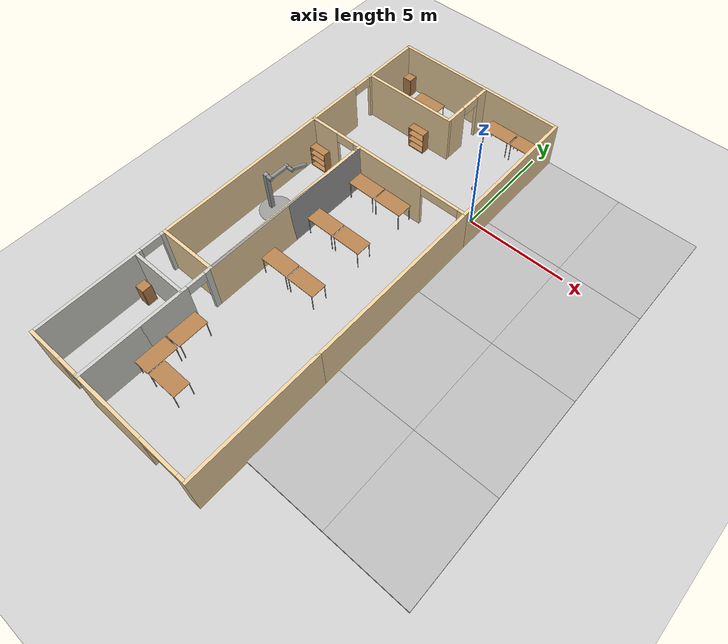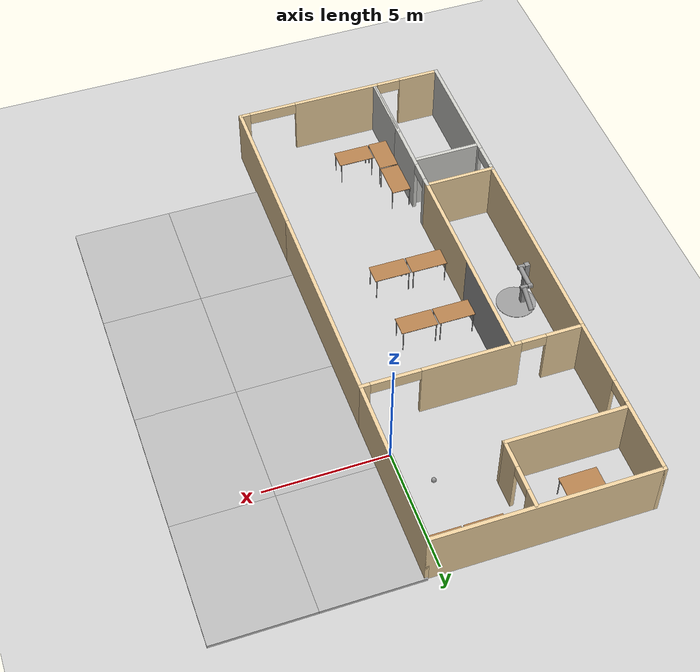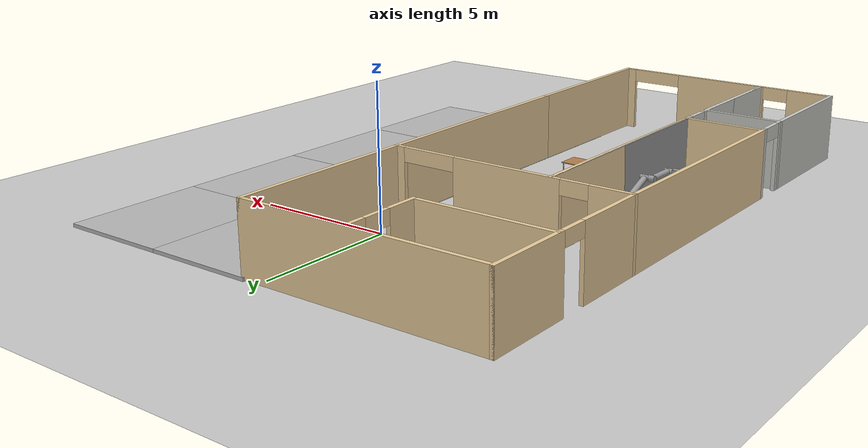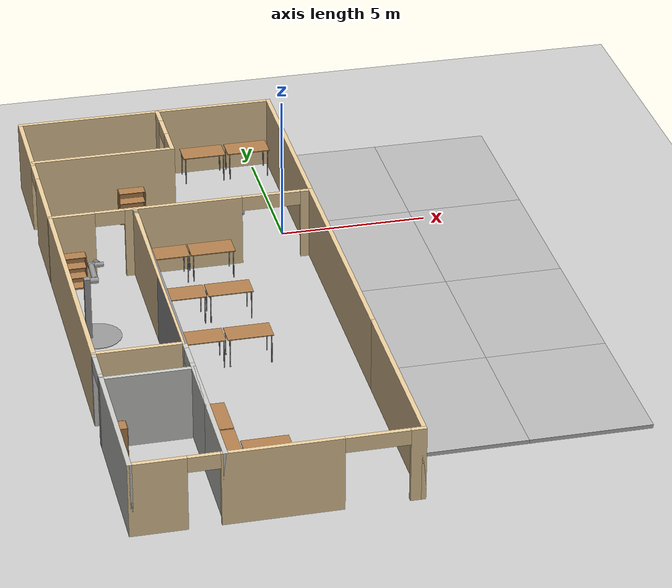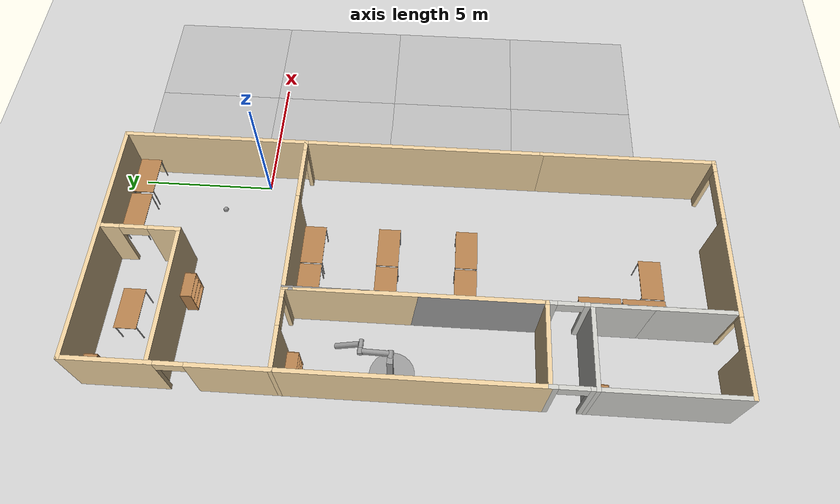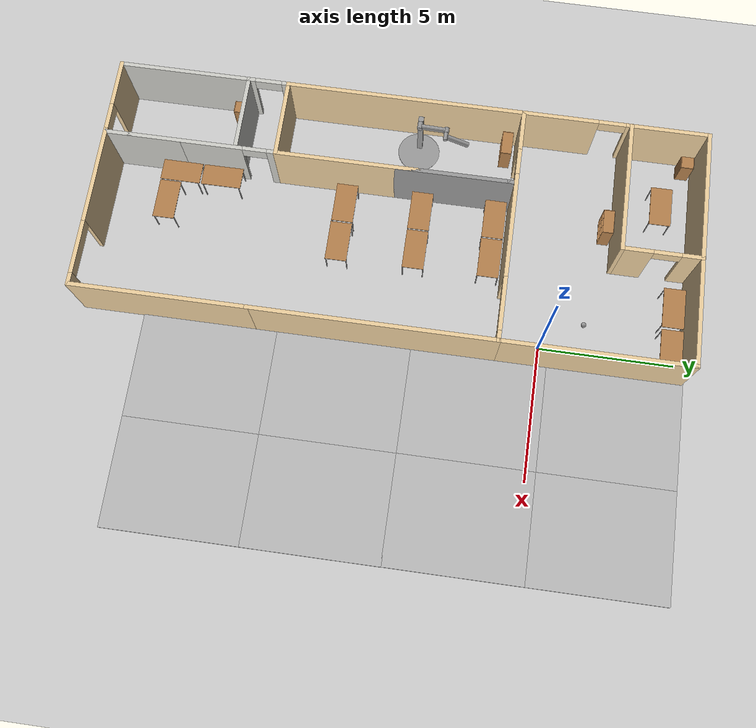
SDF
<sdf version="1.6">
 <world name="default">
  <light name="sun" type="directional">
   <pose>0 0 10 0 -0 0</pose>
   <diffuse>0.8 0.8 0.8 1</diffuse>
   <specular>0.2 0.2 0.2 1</specular>
   <attenuation>
    <range>1000</range>
    <constant>0.9</constant>
    <linear>0.01</linear>
    <quadratic>0.001</quadratic>
   </attenuation>
   <direction>-0.5 0.1 -0.9</direction>
  </light>
  <model name="ground_plane">
   <static>1</static>
   <link name="link">
    <collision name="collision">
     <geometry><plane><normal>0 0 1</normal><size>100 100</size></plane></geometry>
     <surface>
      <contact><collide_bitmask>65535</collide_bitmask></contact>
      <friction><ode><mu>100</mu><mu2>50</mu2></ode></friction>
     </surface>
    </collision>
    <visual name="visual">
     <cast_shadows>0</cast_shadows>
     <geometry><plane><normal>0 0 1</normal><size>100 100</size></plane></geometry>
     <material>
      <script><uri>file://media/materials/scripts/gazebo.material</uri><name>Gazebo/Grey</name></script>
     </material>
    </visual>
   </link>
  </model>
  <gravity>0 0 -9.8</gravity>
  <magnetic_field>6e-06 2.3e-05 -4.2e-05</magnetic_field>
  <atmosphere type="adiabatic"/>
  <physics name="default_physics" default="0" type="ode">
   <max_step_size>0.001</max_step_size>
   <real_time_factor>1</real_time_factor>
   <real_time_update_rate>1000</real_time_update_rate>
  </physics>
  <scene><ambient>0.4 0.4 0.4 1</ambient><background>0.7 0.7 0.7 1</background><shadows>1</shadows></scene>
  <spherical_coordinates>
   <surface_model>EARTH_WGS84</surface_model>
   <latitude_deg>0</latitude_deg>
   <longitude_deg>0</longitude_deg>
   <elevation>0</elevation>
   <heading_deg>0</heading_deg>
  </spherical_coordinates>
  <model name="Building">
   <pose>-3.79491 -5.77885 0 0 -0 0</pose>
   <link name="Wall_50">
    <collision name="Wall_50_Collision">
     <geometry><box><size>9 0.15 2.5</size></box></geometry>
     <pose>0 0 1.25 0 -0 0</pose>
    </collision>
    <visual name="Wall_50_Visual">
     <pose>0 0 1.25 0 -0 0</pose>
     <geometry><box><size>9 0.15 2.5</size></box></geometry>
     <material>
      <script><uri>file://media/materials/scripts/gazebo.material</uri><name>Gazebo/Grey</name></script>
      <ambient>0.921569 0.807843 0.615686 1</ambient>
     </material>
     <meta><layer>0</layer></meta>
    </visual>
    <pose>0 11.025 0 0 -0 0</pose>
   </link>
   <link name="Wall_51">
    <collision name="Wall_51_Collision">
     <geometry><box><size>7 0.15 2.5</size></box></geometry>
     <pose>0 0 1.25 0 -0 0</pose>
    </collision>
    <visual name="Wall_51_Visual">
     <pose>0 0 1.25 0 -0 0</pose>
     <geometry><box><size>7 0.15 2.5</size></box></geometry>
     <material>
      <script><uri>file://media/materials/scripts/gazebo.material</uri><name>Gazebo/Grey</name></script>
      <ambient>0.921569 0.807843 0.615686 1</ambient>
     </material>
     <meta><layer>0</layer></meta>
    </visual>
    <pose>4.425 7.6 0 0 0 -1.5708</pose>
   </link>
   <link name="Wall_52">
    <pose>0 4.175 0 0 -0 3.14159</pose>
    <visual name="Wall_52_Visual_0">
     <pose>-4.28104 0 1.25 0 -0 0</pose>
     <geometry><box><size>0.437917 0.15 2.5</size></box></geometry>
     <material>
      <script><uri>file://media/materials/scripts/gazebo.material</uri><name>Gazebo/Grey</name></script>
      <ambient>0.921569 0.807843 0.615686 1</ambient>
     </material>
     <meta><layer>0</layer></meta>
    </visual>
    <collision name="Wall_52_Collision_0">
     <geometry><box><size>0.437917 0.15 2.5</size></box></geometry>
     <pose>-4.28104 0 1.25 0 -0 0</pose>
    </collision>
    <visual name="Wall_52_Visual_1">
     <pose>-0.067944 0 1.25 0 -0 0</pose>
     <geometry><box><size>3.98828 0.15 2.5</size></box></geometry>
     <material>
      <script><uri>file://media/materials/scripts/gazebo.material</uri><name>Gazebo/Grey</name></script>
      <ambient>0.921569 0.807843 0.615686 1</ambient>
     </material>
     <meta><layer>0</layer></meta>
    </visual>
    <collision name="Wall_52_Collision_1">
     <geometry><box><size>3.98828 0.15 2.5</size></box></geometry>
     <pose>-0.067944 0 1.25 0 -0 0</pose>
    </collision>
    <visual name="Wall_52_Visual_2">
     <pose>3.7131 0 1.25 0 -0 0</pose>
     <geometry><box><size>1.5738 0.15 2.5</size></box></geometry>
     <material>
      <script><uri>file://media/materials/scripts/gazebo.material</uri><name>Gazebo/Grey</name></script>
      <ambient>0.921569 0.807843 0.615686 1</ambient>
     </material>
     <meta><layer>0</layer></meta>
    </visual>
    <collision name="Wall_52_Collision_2">
     <geometry><box><size>1.5738 0.15 2.5</size></box></geometry>
     <pose>3.7131 0 1.25 0 -0 0</pose>
    </collision>
    <visual name="Wall_52_Visual_3">
     <pose>-3.06208 0 2.25 0 -0 0</pose>
     <geometry><box><size>2 0.15 0.5</size></box></geometry>
     <material>
      <script><uri>file://media/materials/scripts/gazebo.material</uri><name>Gazebo/Grey</name></script>
      <ambient>0.921569 0.807843 0.615686 1</ambient>
     </material>
     <meta><layer>0</layer></meta>
    </visual>
    <collision name="Wall_52_Collision_3">
     <geometry><box><size>2 0.15 0.5</size></box></geometry>
     <pose>-3.06208 0 2.25 0 -0 0</pose>
    </collision>
    <visual name="Wall_52_Visual_4">
     <pose>2.4262 0 2.25 0 -0 0</pose>
     <geometry><box><size>1 0.15 0.5</size></box></geometry>
     <material>
      <script><uri>file://media/materials/scripts/gazebo.material</uri><name>Gazebo/Grey</name></script>
      <ambient>0.921569 0.807843 0.615686 1</ambient>
     </material>
     <meta><layer>0</layer></meta>
    </visual>
    <collision name="Wall_52_Collision_4">
     <geometry><box><size>1 0.15 0.5</size></box></geometry>
     <pose>2.4262 0 2.25 0 -0 0</pose>
    </collision>
   </link>
   <link name="Wall_53">
    <pose>-4.425 7.6 0 0 -0 1.5708</pose>
    <visual name="Wall_53_Visual_0">
     <pose>-2.07395 0 1.25 0 -0 0</pose>
     <geometry><box><size>2.8521 0.15 2.5</size></box></geometry>
     <material>
      <script><uri>file://media/materials/scripts/gazebo.material</uri><name>Gazebo/Grey</name></script>
      <ambient>0.921569 0.807843 0.615686 1</ambient>
     </material>
     <meta><layer>0</layer></meta>
    </visual>
    <collision name="Wall_53_Collision_0">
     <geometry><box><size>2.8521 0.15 2.5</size></box></geometry>
     <pose>-2.07395 0 1.25 0 -0 0</pose>
    </collision>
    <visual name="Wall_53_Visual_1">
     <pose>1.92605 0 1.25 0 -0 0</pose>
     <geometry><box><size>3.1479 0.15 2.5</size></box></geometry>
     <material>
      <script><uri>file://media/materials/scripts/gazebo.material</uri><name>Gazebo/Grey</name></script>
      <ambient>0.921569 0.807843 0.615686 1</ambient>
     </material>
     <meta><layer>0</layer></meta>
    </visual>
    <collision name="Wall_53_Collision_1">
     <geometry><box><size>3.1479 0.15 2.5</size></box></geometry>
     <pose>1.92605 0 1.25 0 -0 0</pose>
    </collision>
    <visual name="Wall_53_Visual_2">
     <pose>-0.1479 0 2.25 0 -0 0</pose>
     <geometry><box><size>1 0.15 0.5</size></box></geometry>
     <material>
      <script><uri>file://media/materials/scripts/gazebo.material</uri><name>Gazebo/Grey</name></script>
      <ambient>0.921569 0.807843 0.615686 1</ambient>
     </material>
     <meta><layer>0</layer></meta>
    </visual>
    <collision name="Wall_53_Collision_2">
     <geometry><box><size>1 0.15 0.5</size></box></geometry>
     <pose>-0.1479 0 2.25 0 -0 0</pose>
    </collision>
   </link>
   <link name="Wall_55">
    <collision name="Wall_55_Collision">
     <geometry><box><size>9 0.15 2.5</size></box></geometry>
     <pose>0 0 1.25 0 -0 0</pose>
    </collision>
    <visual name="Wall_55_Visual">
     <pose>0 0 1.25 0 -0 0</pose>
     <geometry><box><size>9 0.15 2.5</size></box></geometry>
     <material>
      <script><uri>file://media/materials/scripts/gazebo.material</uri><name>Gazebo/Grey</name></script>
      <ambient>0.921569 0.807843 0.615686 1</ambient>
     </material>
     <meta><layer>0</layer></meta>
    </visual>
    <pose>-4.425 -0.25 0 0 0 -1.5708</pose>
   </link>
   <link name="Wall_56">
    <collision name="Wall_56_Collision">
     <geometry><box><size>3 0.15 2.5</size></box></geometry>
     <pose>0 0 1.25 0 -0 0</pose>
    </collision>
    <visual name="Wall_56_Visual">
     <pose>0 0 1.25 0 -0 0</pose>
     <geometry><box><size>3 0.15 2.5</size></box></geometry>
     <material>
      <script><uri>file://media/materials/scripts/gazebo.material</uri><name>Gazebo/Grey</name></script>
      <ambient>0.921569 0.807843 0.615686 1</ambient>
     </material>
     <meta><layer>0</layer></meta>
    </visual>
    <pose>-3 -4.675 0 0 -0 0</pose>
   </link>
   <link name="Wall_58">
    <collision name="Wall_58_Collision">
     <geometry><box><size>0.15 0.15 2.5</size></box></geometry>
     <pose>0 0 1.25 0 -0 0</pose>
    </collision>
    <visual name="Wall_58_Visual">
     <pose>0 0 1.25 0 -0 0</pose>
     <geometry><box><size>0.15 0.15 2.5</size></box></geometry>
     <material>
      <script><uri>file://media/materials/scripts/gazebo.material</uri><name>Gazebo/Grey</name></script>
      <ambient>1 1 1 1</ambient>
     </material>
     <meta><layer>0</layer></meta>
    </visual>
    <pose>-1.575 3.925 0 0 -0 0</pose>
   </link>
   <link name="Wall_66">
    <collision name="Wall_66_Collision">
     <geometry><box><size>9 0.15 2.5</size></box></geometry>
     <pose>0 0 1.25 0 -0 0</pose>
    </collision>
    <visual name="Wall_66_Visual">
     <pose>0 0 1.25 0 -0 0</pose>
     <geometry><box><size>9 0.15 2.5</size></box></geometry>
     <material>
      <script><uri>file://media/materials/scripts/gazebo.material</uri><name>Gazebo/Grey</name></script>
      <ambient>0.921569 0.807843 0.615686 1</ambient>
     </material>
     <meta><layer>0</layer></meta>
    </visual>
    <pose>-1.575 -0.25 0 0 -0 1.5708</pose>
   </link>
   <link name="Wall_68">
    <collision name="Wall_68_Collision">
     <geometry><box><size>9 0.15 2.5</size></box></geometry>
     <pose>0 0 1.25 0 -0 0</pose>
    </collision>
    <visual name="Wall_68_Visual">
     <pose>0 0 1.25 0 -0 0</pose>
     <geometry><box><size>9 0.15 2.5</size></box></geometry>
     <material>
      <script><uri>file://media/materials/scripts/gazebo.material</uri><name>Gazebo/Grey</name></script>
      <ambient>0.921569 0.807843 0.615686 1</ambient>
     </material>
     <meta><layer>0</layer></meta>
    </visual>
    <pose>4.425 -0.25 0 0 0 -1.5708</pose>
   </link>
   <link name="Wall_75">
    <collision name="Wall_75_Collision">
     <geometry><box><size>9 0.15 2.5</size></box></geometry>
     <pose>0 0 1.25 0 -0 0</pose>
    </collision>
    <visual name="Wall_75_Visual">
     <pose>0 0 1.25 0 -0 0</pose>
     <geometry><box><size>9 0.15 2.5</size></box></geometry>
     <material>
      <script><uri>file://media/materials/scripts/gazebo.material</uri><name>Gazebo/Grey</name></script>
      <ambient>1 1 1 1</ambient>
     </material>
     <meta><layer>0</layer></meta>
    </visual>
    <pose>-1.575 -0.25 0 0 0 -1.5708</pose>
   </link>
   <link name="Wall_78">
    <pose>-4.425 -7.85 0 0 0 -1.5708</pose>
    <visual name="Wall_78_Visual_0">
     <pose>-3.0867 0 1.25 0 -0 0</pose>
     <geometry><box><size>0.326599 0.15 2.5</size></box></geometry>
     <material>
      <script><uri>file://media/materials/scripts/gazebo.material</uri><name>Gazebo/CeilingTiled</name></script>
      <ambient>0.921569 0.807843 0.615686 1</ambient>
     </material>
     <meta><layer>0</layer></meta>
    </visual>
    <collision name="Wall_78_Collision_0">
     <geometry><box><size>0.326599 0.15 2.5</size></box></geometry>
     <pose>-3.0867 0 1.25 0 -0 0</pose>
    </collision>
    <visual name="Wall_78_Visual_1">
     <pose>0.6633 0 1.25 0 -0 0</pose>
     <geometry><box><size>5.1734 0.15 2.5</size></box></geometry>
     <material>
      <script><uri>file://media/materials/scripts/gazebo.material</uri><name>Gazebo/CeilingTiled</name></script>
      <ambient>0.921569 0.807843 0.615686 1</ambient>
     </material>
     <meta><layer>0</layer></meta>
    </visual>
    <collision name="Wall_78_Collision_1">
     <geometry><box><size>5.1734 0.15 2.5</size></box></geometry>
     <pose>0.6633 0 1.25 0 -0 0</pose>
    </collision>
    <visual name="Wall_78_Visual_2">
     <pose>-2.4234 0 2.25 0 -0 0</pose>
     <geometry><box><size>1 0.15 0.5</size></box></geometry>
     <material>
      <script><uri>file://media/materials/scripts/gazebo.material</uri><name>Gazebo/CeilingTiled</name></script>
      <ambient>0.921569 0.807843 0.615686 1</ambient>
     </material>
     <meta><layer>0</layer></meta>
    </visual>
    <collision name="Wall_78_Collision_2">
     <geometry><box><size>1 0.15 0.5</size></box></geometry>
     <pose>-2.4234 0 2.25 0 -0 0</pose>
    </collision>
   </link>
   <link name="Wall_80">
    <pose>0 -11.025 0 0 -0 0</pose>
    <visual name="Wall_80_Visual_0">
     <pose>-3.60666 0 1.25 0 -0 0</pose>
     <geometry><box><size>1.78667 0.15 2.5</size></box></geometry>
     <material>
      <script><uri>file://media/materials/scripts/gazebo.material</uri><name>Gazebo/Grey</name></script>
      <ambient>0.921569 0.807843 0.615686 1</ambient>
     </material>
     <meta><layer>0</layer></meta>
    </visual>
    <collision name="Wall_80_Collision_0">
     <geometry><box><size>1.78667 0.15 2.5</size></box></geometry>
     <pose>-3.60666 0 1.25 0 -0 0</pose>
    </collision>
    <visual name="Wall_80_Visual_1">
     <pose>0.15254 0 1.25 0 -0 0</pose>
     <geometry><box><size>3.73174 0.15 2.5</size></box></geometry>
     <material>
      <script><uri>file://media/materials/scripts/gazebo.material</uri><name>Gazebo/Grey</name></script>
      <ambient>0.921569 0.807843 0.615686 1</ambient>
     </material>
     <meta><layer>0</layer></meta>
    </visual>
    <collision name="Wall_80_Collision_1">
     <geometry><box><size>3.73174 0.15 2.5</size></box></geometry>
     <pose>0.15254 0 1.25 0 -0 0</pose>
    </collision>
    <visual name="Wall_80_Visual_2">
     <pose>4.2592 0 1.25 0 -0 0</pose>
     <geometry><box><size>0.481591 0.15 2.5</size></box></geometry>
     <material>
      <script><uri>file://media/materials/scripts/gazebo.material</uri><name>Gazebo/Grey</name></script>
      <ambient>0.921569 0.807843 0.615686 1</ambient>
     </material>
     <meta><layer>0</layer></meta>
    </visual>
    <collision name="Wall_80_Collision_2">
     <geometry><box><size>0.481591 0.15 2.5</size></box></geometry>
     <pose>4.2592 0 1.25 0 -0 0</pose>
    </collision>
    <visual name="Wall_80_Visual_3">
     <pose>-2.21333 0 2.25 0 -0 0</pose>
     <geometry><box><size>1 0.15 0.5</size></box></geometry>
     <material>
      <script><uri>file://media/materials/scripts/gazebo.material</uri><name>Gazebo/Grey</name></script>
      <ambient>0.921569 0.807843 0.615686 1</ambient>
     </material>
     <meta><layer>0</layer></meta>
    </visual>
    <collision name="Wall_80_Collision_3">
     <geometry><box><size>1 0.15 0.5</size></box></geometry>
     <pose>-2.21333 0 2.25 0 -0 0</pose>
    </collision>
    <visual name="Wall_80_Visual_4">
     <pose>3.01841 0 2.25 0 -0 0</pose>
     <geometry><box><size>2 0.15 0.5</size></box></geometry>
     <material>
      <script><uri>file://media/materials/scripts/gazebo.material</uri><name>Gazebo/Grey</name></script>
      <ambient>0.921569 0.807843 0.615686 1</ambient>
     </material>
     <meta><layer>0</layer></meta>
    </visual>
    <collision name="Wall_80_Collision_4">
     <geometry><box><size>2 0.15 0.5</size></box></geometry>
     <pose>3.01841 0 2.25 0 -0 0</pose>
    </collision>
   </link>
   <link name="Wall_82">
    <collision name="Wall_82_Collision">
     <geometry><box><size>6.5 0.15 2.5</size></box></geometry>
     <pose>0 0 1.25 0 -0 0</pose>
    </collision>
    <visual name="Wall_82_Visual">
     <pose>0 0 1.25 0 -0 0</pose>
     <geometry><box><size>6.5 0.15 2.5</size></box></geometry>
     <material>
      <script><uri>file://media/materials/scripts/gazebo.material</uri><name>Gazebo/Grey</name></script>
      <ambient>0.921569 0.807843 0.615686 1</ambient>
     </material>
     <meta><layer>0</layer></meta>
    </visual>
    <pose>4.425 -7.85 0 0 -0 1.5708</pose>
   </link>
   <link name="Wall_84">
    <pose>-1.575 -7.85 0 0 0 -1.5708</pose>
    <visual name="Wall_84_Visual_0">
     <pose>-3.04772 0 1.25 0 -0 0</pose>
     <geometry><box><size>0.404569 0.15 2.5</size></box></geometry>
     <material>
      <script><uri>file://media/materials/scripts/gazebo.material</uri><name>Gazebo/CeilingTiled</name></script>
      <ambient>0.921569 0.807843 0.615686 1</ambient>
     </material>
     <meta><layer>0</layer></meta>
    </visual>
    <collision name="Wall_84_Collision_0">
     <geometry><box><size>0.404569 0.15 2.5</size></box></geometry>
     <pose>-3.04772 0 1.25 0 -0 0</pose>
    </collision>
    <visual name="Wall_84_Visual_1">
     <pose>0.652285 0 1.25 0 -0 0</pose>
     <geometry><box><size>5.19543 0.15 2.5</size></box></geometry>
     <material>
      <script><uri>file://media/materials/scripts/gazebo.material</uri><name>Gazebo/CeilingTiled</name></script>
      <ambient>0.921569 0.807843 0.615686 1</ambient>
     </material>
     <meta><layer>0</layer></meta>
    </visual>
    <collision name="Wall_84_Collision_1">
     <geometry><box><size>5.19543 0.15 2.5</size></box></geometry>
     <pose>0.652285 0 1.25 0 -0 0</pose>
    </collision>
    <visual name="Wall_84_Visual_2">
     <pose>-2.39543 0 2.25 0 -0 0</pose>
     <geometry><box><size>0.9 0.15 0.5</size></box></geometry>
     <material>
      <script><uri>file://media/materials/scripts/gazebo.material</uri><name>Gazebo/CeilingTiled</name></script>
      <ambient>0.921569 0.807843 0.615686 1</ambient>
     </material>
     <meta><layer>0</layer></meta>
    </visual>
    <collision name="Wall_84_Collision_2">
     <geometry><box><size>0.9 0.15 0.5</size></box></geometry>
     <pose>-2.39543 0 2.25 0 -0 0</pose>
    </collision>
   </link>
   <link name="Wall_86">
    <collision name="Wall_86_Collision">
     <geometry><box><size>5 0.15 2.5</size></box></geometry>
     <pose>0 0 1.25 0 -0 0</pose>
    </collision>
    <visual name="Wall_86_Visual">
     <pose>0 0 1.25 0 -0 0</pose>
     <geometry><box><size>5 0.15 2.5</size></box></geometry>
     <material>
      <script><uri>file://media/materials/scripts/gazebo.material</uri><name>Gazebo/CeilingTiled</name></script>
      <ambient>0.921569 0.807843 0.615686 1</ambient>
     </material>
     <meta><layer>0</layer></meta>
    </visual>
    <pose>-1.575 -8.6 0 0 -0 1.5708</pose>
   </link>
   <link name="Wall_89">
    <collision name="Wall_89_Collision">
     <geometry><box><size>3 0.15 2.5</size></box></geometry>
     <pose>0 0 1.25 0 -0 0</pose>
    </collision>
    <visual name="Wall_89_Visual">
     <pose>0 0 1.25 0 -0 0</pose>
     <geometry><box><size>3 0.15 2.5</size></box></geometry>
     <material>
      <script><uri>file://media/materials/scripts/gazebo.material</uri><name>Gazebo/CeilingTiled</name></script>
      <ambient>0.921569 0.807843 0.615686 1</ambient>
     </material>
     <meta><layer>0</layer></meta>
    </visual>
    <pose>-3 -6.175 0 0 -0 3.14159</pose>
   </link>
   <link name="Wall_91">
    <pose>0.429416 9.58905 0 0 0 -1.5708</pose>
    <visual name="Wall_91_Visual_0">
     <pose>-1.09544 0 1.25 0 -0 0</pose>
     <geometry><box><size>0.809125 0.15 2.5</size></box></geometry>
     <material>
      <script><uri>file://media/materials/scripts/gazebo.material</uri><name>Gazebo/Grey</name></script>
      <ambient>0.921569 0.807843 0.615686 1</ambient>
     </material>
     <meta><layer>0</layer></meta>
    </visual>
    <collision name="Wall_91_Collision_0">
     <geometry><box><size>0.809125 0.15 2.5</size></box></geometry>
     <pose>-1.09544 0 1.25 0 -0 0</pose>
    </collision>
    <visual name="Wall_91_Visual_1">
     <pose>0.904562 0 1.25 0 -0 0</pose>
     <geometry><box><size>1.19087 0.15 2.5</size></box></geometry>
     <material>
      <script><uri>file://media/materials/scripts/gazebo.material</uri><name>Gazebo/Grey</name></script>
      <ambient>0.921569 0.807843 0.615686 1</ambient>
     </material>
     <meta><layer>0</layer></meta>
    </visual>
    <collision name="Wall_91_Collision_1">
     <geometry><box><size>1.19087 0.15 2.5</size></box></geometry>
     <pose>0.904562 0 1.25 0 -0 0</pose>
    </collision>
    <visual name="Wall_91_Visual_2">
     <pose>-0.190875 0 2.25 0 -0 0</pose>
     <geometry><box><size>1 0.15 0.5</size></box></geometry>
     <material>
      <script><uri>file://media/materials/scripts/gazebo.material</uri><name>Gazebo/Grey</name></script>
      <ambient>0.921569 0.807843 0.615686 1</ambient>
     </material>
     <meta><layer>0</layer></meta>
    </visual>
    <collision name="Wall_91_Collision_2">
     <geometry><box><size>1 0.15 0.5</size></box></geometry>
     <pose>-0.190875 0 2.25 0 -0 0</pose>
    </collision>
   </link>
   <link name="Wall_92">
    <collision name="Wall_92_Collision">
     <geometry><box><size>5 0.15 2.5</size></box></geometry>
     <pose>0 0 1.25 0 -0 0</pose>
    </collision>
    <visual name="Wall_92_Visual">
     <pose>0 0 1.25 0 -0 0</pose>
     <geometry><box><size>5 0.15 2.5</size></box></geometry>
     <material>
      <script><uri>file://media/materials/scripts/gazebo.material</uri><name>Gazebo/Grey</name></script>
      <ambient>0.921569 0.807843 0.615686 1</ambient>
     </material>
     <meta><layer>0</layer></meta>
    </visual>
    <pose>-1.99558 8.16405 0 0 -0 3.14159</pose>
   </link>
   <static>1</static>
  </model>
  <model name="cabinet">
   <static>1</static>
   <link name="cabinet_bottom_plate">
    <inertial>
     <pose>0 0 -1 0 -0 0</pose>
     <inertia><ixx>2.05</ixx><ixy>0</ixy><ixz>0</ixz><iyy>2.05</iyy><iyz>0</iyz><izz>2.05</izz></inertia>
     <mass>25</mass>
    </inertial>
    <collision name="cabinet_bottom_plate_geom">
     <pose>0 0 0.01 0 -0 0</pose>
     <geometry><box><size>0.45 0.45 0.02</size></box></geometry>
    </collision>
    <visual name="cabinet_bottom_plate_geom_visual">
     <pose>0 0 0.01 0 -0 0</pose>
     <geometry><box><size>0.45 0.45 0.02</size></box></geometry>
     <material>
      <script><uri>file://media/materials/scripts/gazebo.material</uri><name>Gazebo/Wood</name></script>
     </material>
    </visual>
    <collision name="cabinet_bottom_plate_geom_cabinet_back_plate">
     <pose>0.235 0 0.51 0 -0 0</pose>
     <geometry><box><size>0.02 0.45 1.02</size></box></geometry>
    </collision>
    <visual name="cabinet_bottom_plate_geom_cabinet_back_plate_visual">
     <pose>0.235 0 0.51 0 -0 0</pose>
     <geometry><box><size>0.02 0.45 1.02</size></box></geometry>
     <material>
      <script><uri>file://media/materials/scripts/gazebo.material</uri><name>Gazebo/Wood</name></script>
     </material>
    </visual>
    <collision name="cabinet_bottom_plate_geom_cabinet_left_plate">
     <pose>0 0.235 0.51 0 -0 0</pose>
     <geometry><box><size>0.45 0.02 1.02</size></box></geometry>
    </collision>
    <visual name="cabinet_bottom_plate_geom_cabinet_left_plate_visual">
     <pose>0 0.235 0.51 0 -0 0</pose>
     <geometry><box><size>0.45 0.02 1.02</size></box></geometry>
     <material>
      <script><uri>file://media/materials/scripts/gazebo.material</uri><name>Gazebo/Wood</name></script>
     </material>
    </visual>
    <collision name="cabinet_bottom_plate_geom_cabinet_middle_plate">
     <pose>0 0 0.51 0 -0 0</pose>
     <geometry><box><size>0.45 0.45 0.02</size></box></geometry>
    </collision>
    <visual name="cabinet_bottom_plate_geom_cabinet_middle_plate_visual">
     <pose>0 0 0.51 0 -0 0</pose>
     <geometry><box><size>0.45 0.45 0.02</size></box></geometry>
     <material>
      <script><uri>file://media/materials/scripts/gazebo.material</uri><name>Gazebo/Wood</name></script>
     </material>
    </visual>
    <collision name="cabinet_bottom_plate_geom_cabinet_right_plate">
     <pose>0 -0.235 0.51 0 -0 0</pose>
     <geometry><box><size>0.45 0.02 1.02</size></box></geometry>
    </collision>
    <visual name="cabinet_bottom_plate_geom_cabinet_right_plate_visual">
     <pose>0 -0.235 0.51 0 -0 0</pose>
     <geometry><box><size>0.45 0.02 1.02</size></box></geometry>
     <material>
      <script><uri>file://media/materials/scripts/gazebo.material</uri><name>Gazebo/Wood</name></script>
     </material>
    </visual>
    <collision name="cabinet_bottom_plate_geom_cabinet_top_plate">
     <pose>0 0 1.01 0 -0 0</pose>
     <geometry><box><size>0.45 0.45 0.02</size></box></geometry>
    </collision>
    <visual name="cabinet_bottom_plate_geom_cabinet_top_plate_visual">
     <pose>0 0 1.01 0 -0 0</pose>
     <geometry><box><size>0.45 0.45 0.02</size></box></geometry>
     <material>
      <script><uri>file://media/materials/scripts/gazebo.material</uri><name>Gazebo/Wood</name></script>
     </material>
    </visual>
   </link>
   <pose>-7.79073 4.85276 0 0 -0 0</pose>
  </model>
  <model name="bookshelf">
   <static>1</static>
   <link name="link">
    <inertial><mass>1</mass></inertial>
    <collision name="back">
     <pose>0 0.005 0.6 0 -0 0</pose>
     <geometry><box><size>0.9 0.01 1.2</size></box></geometry>
    </collision>
    <visual name="visual1">
     <pose>0 0.005 0.6 0 -0 0</pose>
     <geometry><box><size>0.9 0.01 1.2</size></box></geometry>
     <material>
      <script><uri>file://media/materials/scripts/gazebo.material</uri><name>Gazebo/Wood</name></script>
     </material>
    </visual>
    <collision name="left_side">
     <pose>0.45 -0.195 0.6 0 -0 0</pose>
     <geometry><box><size>0.02 0.4 1.2</size></box></geometry>
    </collision>
    <visual name="visual2">
     <pose>0.45 -0.195 0.6 0 -0 0</pose>
     <geometry><box><size>0.02 0.4 1.2</size></box></geometry>
     <material>
      <script><uri>file://media/materials/scripts/gazebo.material</uri><name>Gazebo/Wood</name></script>
     </material>
    </visual>
    <collision name="right_side">
     <pose>-0.45 -0.195 0.6 0 -0 0</pose>
     <geometry><box><size>0.02 0.4 1.2</size></box></geometry>
    </collision>
    <visual name="visual3">
     <pose>-0.45 -0.195 0.6 0 -0 0</pose>
     <geometry><box><size>0.02 0.4 1.2</size></box></geometry>
     <material>
      <script><uri>file://media/materials/scripts/gazebo.material</uri><name>Gazebo/Wood</name></script>
     </material>
    </visual>
    <collision name="bottom">
     <pose>0 -0.195 0.03 0 -0 0</pose>
     <geometry><box><size>0.88 0.4 0.06</size></box></geometry>
    </collision>
    <visual name="visual4">
     <pose>0 -0.195 0.03 0 -0 0</pose>
     <geometry><box><size>0.88 0.4 0.06</size></box></geometry>
     <material>
      <script><uri>file://media/materials/scripts/gazebo.material</uri><name>Gazebo/Wood</name></script>
     </material>
    </visual>
    <collision name="top">
     <pose>0 -0.195 1.19 0 -0 0</pose>
     <geometry><box><size>0.88 0.4 0.02</size></box></geometry>
    </collision>
    <visual name="visual5">
     <pose>0 -0.195 1.19 0 -0 0</pose>
     <geometry><box><size>0.88 0.4 0.02</size></box></geometry>
     <material>
      <script><uri>file://media/materials/scripts/gazebo.material</uri><name>Gazebo/Wood</name></script>
     </material>
    </visual>
    <collision name="low_shelf">
     <pose>0 -0.195 0.43 0 -0 0</pose>
     <geometry><box><size>0.88 0.4 0.02</size></box></geometry>
    </collision>
    <visual name="visual6">
     <pose>0 -0.195 0.43 0 -0 0</pose>
     <geometry><box><size>0.88 0.4 0.02</size></box></geometry>
     <material>
      <script><uri>file://media/materials/scripts/gazebo.material</uri><name>Gazebo/Wood</name></script>
     </material>
    </visual>
    <collision name="high_shelf">
     <pose>0 -0.195 0.8 0 -0 0</pose>
     <geometry><box><size>0.88 0.4 0.02</size></box></geometry>
    </collision>
    <visual name="visual7">
     <pose>0 -0.195 0.8 0 -0 0</pose>
     <geometry><box><size>0.88 0.4 0.02</size></box></geometry>
     <material>
      <script><uri>file://media/materials/scripts/gazebo.material</uri><name>Gazebo/Wood</name></script>
     </material>
    </visual>
   </link>
   <pose>-4.88239 2.23385 0 0 -0 0</pose>
  </model>
  <model name="table">
   <static>1</static>
   <link name="link">
    <collision name="surface">
     <pose>0 0 1 0 -0 0</pose>
     <geometry><box><size>1.5 0.8 0.03</size></box></geometry>
     <surface><friction><ode><mu>0.6</mu><mu2>0.6</mu2></ode></friction></surface>
    </collision>
    <visual name="visual1">
     <pose>0 0 1 0 -0 0</pose>
     <geometry><box><size>1.5 0.8 0.03</size></box></geometry>
     <material>
      <script><uri>file://media/materials/scripts/gazebo.material</uri><name>Gazebo/Wood</name></script>
     </material>
    </visual>
    <collision name="front_left_leg">
     <pose>0.68 0.38 0.5 0 -0 0</pose>
     <geometry><cylinder><radius>0.02</radius><length>1</length></cylinder></geometry>
    </collision>
    <visual name="front_left_leg">
     <pose>0.68 0.38 0.5 0 -0 0</pose>
     <geometry><cylinder><radius>0.02</radius><length>1</length></cylinder></geometry>
     <material>
      <script><uri>file://media/materials/scripts/gazebo.material</uri><name>Gazebo/Grey</name></script>
     </material>
    </visual>
    <collision name="front_right_leg">
     <pose>0.68 -0.38 0.5 0 -0 0</pose>
     <geometry><cylinder><radius>0.02</radius><length>1</length></cylinder></geometry>
    </collision>
    <visual name="front_right_leg">
     <pose>0.68 -0.38 0.5 0 -0 0</pose>
     <geometry><cylinder><radius>0.02</radius><length>1</length></cylinder></geometry>
     <material>
      <script><uri>file://media/materials/scripts/gazebo.material</uri><name>Gazebo/Grey</name></script>
     </material>
    </visual>
    <collision name="back_right_leg">
     <pose>-0.68 -0.38 0.5 0 -0 0</pose>
     <geometry><cylinder><radius>0.02</radius><length>1</length></cylinder></geometry>
    </collision>
    <visual name="back_right_leg">
     <pose>-0.68 -0.38 0.5 0 -0 0</pose>
     <geometry><cylinder><radius>0.02</radius><length>1</length></cylinder></geometry>
     <material>
      <script><uri>file://media/materials/scripts/gazebo.material</uri><name>Gazebo/Grey</name></script>
     </material>
    </visual>
    <collision name="back_left_leg">
     <pose>-0.68 0.38 0.5 0 -0 0</pose>
     <geometry><cylinder><radius>0.02</radius><length>1</length></cylinder></geometry>
    </collision>
    <visual name="back_left_leg">
     <pose>-0.68 0.38 0.5 0 -0 0</pose>
     <geometry><cylinder><radius>0.02</radius><length>1</length></cylinder></geometry>
     <material>
      <script><uri>file://media/materials/scripts/gazebo.material</uri><name>Gazebo/Grey</name></script>
     </material>
    </visual>
   </link>
   <pose>-5.82965 3.95107 0 0 -0 0</pose>
  </model>
  <model name="table_0">
   <static>1</static>
   <link name="link">
    <collision name="surface">
     <pose>0 0 1 0 -0 0</pose>
     <geometry><box><size>1.5 0.8 0.03</size></box></geometry>
     <surface><friction><ode><mu>0.6</mu><mu2>0.6</mu2></ode></friction></surface>
    </collision>
    <visual name="visual1">
     <pose>0 0 1 0 -0 0</pose>
     <geometry><box><size>1.5 0.8 0.03</size></box></geometry>
     <material>
      <script><uri>file://media/materials/scripts/gazebo.material</uri><name>Gazebo/Wood</name></script>
     </material>
    </visual>
    <collision name="front_left_leg">
     <pose>0.68 0.38 0.5 0 -0 0</pose>
     <geometry><cylinder><radius>0.02</radius><length>1</length></cylinder></geometry>
    </collision>
    <visual name="front_left_leg">
     <pose>0.68 0.38 0.5 0 -0 0</pose>
     <geometry><cylinder><radius>0.02</radius><length>1</length></cylinder></geometry>
     <material>
      <script><uri>file://media/materials/scripts/gazebo.material</uri><name>Gazebo/Grey</name></script>
     </material>
    </visual>
    <collision name="front_right_leg">
     <pose>0.68 -0.38 0.5 0 -0 0</pose>
     <geometry><cylinder><radius>0.02</radius><length>1</length></cylinder></geometry>
    </collision>
    <visual name="front_right_leg">
     <pose>0.68 -0.38 0.5 0 -0 0</pose>
     <geometry><cylinder><radius>0.02</radius><length>1</length></cylinder></geometry>
     <material>
      <script><uri>file://media/materials/scripts/gazebo.material</uri><name>Gazebo/Grey</name></script>
     </material>
    </visual>
    <collision name="back_right_leg">
     <pose>-0.68 -0.38 0.5 0 -0 0</pose>
     <geometry><cylinder><radius>0.02</radius><length>1</length></cylinder></geometry>
    </collision>
    <visual name="back_right_leg">
     <pose>-0.68 -0.38 0.5 0 -0 0</pose>
     <geometry><cylinder><radius>0.02</radius><length>1</length></cylinder></geometry>
     <material>
      <script><uri>file://media/materials/scripts/gazebo.material</uri><name>Gazebo/Grey</name></script>
     </material>
    </visual>
    <collision name="back_left_leg">
     <pose>-0.68 0.38 0.5 0 -0 0</pose>
     <geometry><cylinder><radius>0.02</radius><length>1</length></cylinder></geometry>
    </collision>
    <visual name="back_left_leg">
     <pose>-0.68 0.38 0.5 0 -0 0</pose>
     <geometry><cylinder><radius>0.02</radius><length>1</length></cylinder></geometry>
     <material>
      <script><uri>file://media/materials/scripts/gazebo.material</uri><name>Gazebo/Grey</name></script>
     </material>
    </visual>
   </link>
   <pose>-0.288993 4.6714 0 0 -0 0</pose>
  </model>
  <model name="table_1">
   <static>1</static>
   <link name="link">
    <collision name="surface">
     <pose>0 0 1 0 -0 0</pose>
     <geometry><box><size>1.5 0.8 0.03</size></box></geometry>
     <surface><friction><ode><mu>0.6</mu><mu2>0.6</mu2></ode></friction></surface>
    </collision>
    <visual name="visual1">
     <pose>0 0 1 0 -0 0</pose>
     <geometry><box><size>1.5 0.8 0.03</size></box></geometry>
     <material>
      <script><uri>file://media/materials/scripts/gazebo.material</uri><name>Gazebo/Wood</name></script>
     </material>
    </visual>
    <collision name="front_left_leg">
     <pose>0.68 0.38 0.5 0 -0 0</pose>
     <geometry><cylinder><radius>0.02</radius><length>1</length></cylinder></geometry>
    </collision>
    <visual name="front_left_leg">
     <pose>0.68 0.38 0.5 0 -0 0</pose>
     <geometry><cylinder><radius>0.02</radius><length>1</length></cylinder></geometry>
     <material>
      <script><uri>file://media/materials/scripts/gazebo.material</uri><name>Gazebo/Grey</name></script>
     </material>
    </visual>
    <collision name="front_right_leg">
     <pose>0.68 -0.38 0.5 0 -0 0</pose>
     <geometry><cylinder><radius>0.02</radius><length>1</length></cylinder></geometry>
    </collision>
    <visual name="front_right_leg">
     <pose>0.68 -0.38 0.5 0 -0 0</pose>
     <geometry><cylinder><radius>0.02</radius><length>1</length></cylinder></geometry>
     <material>
      <script><uri>file://media/materials/scripts/gazebo.material</uri><name>Gazebo/Grey</name></script>
     </material>
    </visual>
    <collision name="back_right_leg">
     <pose>-0.68 -0.38 0.5 0 -0 0</pose>
     <geometry><cylinder><radius>0.02</radius><length>1</length></cylinder></geometry>
    </collision>
    <visual name="back_right_leg">
     <pose>-0.68 -0.38 0.5 0 -0 0</pose>
     <geometry><cylinder><radius>0.02</radius><length>1</length></cylinder></geometry>
     <material>
      <script><uri>file://media/materials/scripts/gazebo.material</uri><name>Gazebo/Grey</name></script>
     </material>
    </visual>
    <collision name="back_left_leg">
     <pose>-0.68 0.38 0.5 0 -0 0</pose>
     <geometry><cylinder><radius>0.02</radius><length>1</length></cylinder></geometry>
    </collision>
    <visual name="back_left_leg">
     <pose>-0.68 0.38 0.5 0 -0 0</pose>
     <geometry><cylinder><radius>0.02</radius><length>1</length></cylinder></geometry>
     <material>
      <script><uri>file://media/materials/scripts/gazebo.material</uri><name>Gazebo/Grey</name></script>
     </material>
    </visual>
   </link>
   <pose>-1.87609 4.67031 0 0 -0 0</pose>
  </model>
  <model name="table_2">
   <static>1</static>
   <link name="link">
    <collision name="surface">
     <pose>0 0 1 0 -0 0</pose>
     <geometry><box><size>1.5 0.8 0.03</size></box></geometry>
     <surface><friction><ode><mu>0.6</mu><mu2>0.6</mu2></ode></friction></surface>
    </collision>
    <visual name="visual1">
     <pose>0 0 1 0 -0 0</pose>
     <geometry><box><size>1.5 0.8 0.03</size></box></geometry>
     <material>
      <script><uri>file://media/materials/scripts/gazebo.material</uri><name>Gazebo/Wood</name></script>
     </material>
    </visual>
    <collision name="front_left_leg">
     <pose>0.68 0.38 0.5 0 -0 0</pose>
     <geometry><cylinder><radius>0.02</radius><length>1</length></cylinder></geometry>
    </collision>
    <visual name="front_left_leg">
     <pose>0.68 0.38 0.5 0 -0 0</pose>
     <geometry><cylinder><radius>0.02</radius><length>1</length></cylinder></geometry>
     <material>
      <script><uri>file://media/materials/scripts/gazebo.material</uri><name>Gazebo/Grey</name></script>
     </material>
    </visual>
    <collision name="front_right_leg">
     <pose>0.68 -0.38 0.5 0 -0 0</pose>
     <geometry><cylinder><radius>0.02</radius><length>1</length></cylinder></geometry>
    </collision>
    <visual name="front_right_leg">
     <pose>0.68 -0.38 0.5 0 -0 0</pose>
     <geometry><cylinder><radius>0.02</radius><length>1</length></cylinder></geometry>
     <material>
      <script><uri>file://media/materials/scripts/gazebo.material</uri><name>Gazebo/Grey</name></script>
     </material>
    </visual>
    <collision name="back_right_leg">
     <pose>-0.68 -0.38 0.5 0 -0 0</pose>
     <geometry><cylinder><radius>0.02</radius><length>1</length></cylinder></geometry>
    </collision>
    <visual name="back_right_leg">
     <pose>-0.68 -0.38 0.5 0 -0 0</pose>
     <geometry><cylinder><radius>0.02</radius><length>1</length></cylinder></geometry>
     <material>
      <script><uri>file://media/materials/scripts/gazebo.material</uri><name>Gazebo/Grey</name></script>
     </material>
    </visual>
    <collision name="back_left_leg">
     <pose>-0.68 0.38 0.5 0 -0 0</pose>
     <geometry><cylinder><radius>0.02</radius><length>1</length></cylinder></geometry>
    </collision>
    <visual name="back_left_leg">
     <pose>-0.68 0.38 0.5 0 -0 0</pose>
     <geometry><cylinder><radius>0.02</radius><length>1</length></cylinder></geometry>
     <material>
      <script><uri>file://media/materials/scripts/gazebo.material</uri><name>Gazebo/Grey</name></script>
     </material>
    </visual>
   </link>
   <pose>-4.46585 -2.17895 0 0 -0 0</pose>
  </model>
  <model name="table_3">
   <static>1</static>
   <link name="link">
    <collision name="surface">
     <pose>0 0 1 0 -0 0</pose>
     <geometry><box><size>1.5 0.8 0.03</size></box></geometry>
     <surface><friction><ode><mu>0.6</mu><mu2>0.6</mu2></ode></friction></surface>
    </collision>
    <visual name="visual1">
     <pose>0 0 1 0 -0 0</pose>
     <geometry><box><size>1.5 0.8 0.03</size></box></geometry>
     <material>
      <script><uri>file://media/materials/scripts/gazebo.material</uri><name>Gazebo/Wood</name></script>
     </material>
    </visual>
    <collision name="front_left_leg">
     <pose>0.68 0.38 0.5 0 -0 0</pose>
     <geometry><cylinder><radius>0.02</radius><length>1</length></cylinder></geometry>
    </collision>
    <visual name="front_left_leg">
     <pose>0.68 0.38 0.5 0 -0 0</pose>
     <geometry><cylinder><radius>0.02</radius><length>1</length></cylinder></geometry>
     <material>
      <script><uri>file://media/materials/scripts/gazebo.material</uri><name>Gazebo/Grey</name></script>
     </material>
    </visual>
    <collision name="front_right_leg">
     <pose>0.68 -0.38 0.5 0 -0 0</pose>
     <geometry><cylinder><radius>0.02</radius><length>1</length></cylinder></geometry>
    </collision>
    <visual name="front_right_leg">
     <pose>0.68 -0.38 0.5 0 -0 0</pose>
     <geometry><cylinder><radius>0.02</radius><length>1</length></cylinder></geometry>
     <material>
      <script><uri>file://media/materials/scripts/gazebo.material</uri><name>Gazebo/Grey</name></script>
     </material>
    </visual>
    <collision name="back_right_leg">
     <pose>-0.68 -0.38 0.5 0 -0 0</pose>
     <geometry><cylinder><radius>0.02</radius><length>1</length></cylinder></geometry>
    </collision>
    <visual name="back_right_leg">
     <pose>-0.68 -0.38 0.5 0 -0 0</pose>
     <geometry><cylinder><radius>0.02</radius><length>1</length></cylinder></geometry>
     <material>
      <script><uri>file://media/materials/scripts/gazebo.material</uri><name>Gazebo/Grey</name></script>
     </material>
    </visual>
    <collision name="back_left_leg">
     <pose>-0.68 0.38 0.5 0 -0 0</pose>
     <geometry><cylinder><radius>0.02</radius><length>1</length></cylinder></geometry>
    </collision>
    <visual name="back_left_leg">
     <pose>-0.68 0.38 0.5 0 -0 0</pose>
     <geometry><cylinder><radius>0.02</radius><length>1</length></cylinder></geometry>
     <material>
      <script><uri>file://media/materials/scripts/gazebo.material</uri><name>Gazebo/Grey</name></script>
     </material>
    </visual>
   </link>
   <pose>-2.91567 -2.17764 0 0 -0 0</pose>
  </model>
  <model name="table_4">
   <static>1</static>
   <link name="link">
    <collision name="surface">
     <pose>0 0 1 0 -0 0</pose>
     <geometry><box><size>1.5 0.8 0.03</size></box></geometry>
     <surface><friction><ode><mu>0.6</mu><mu2>0.6</mu2></ode></friction></surface>
    </collision>
    <visual name="visual1">
     <pose>0 0 1 0 -0 0</pose>
     <geometry><box><size>1.5 0.8 0.03</size></box></geometry>
     <material>
      <script><uri>file://media/materials/scripts/gazebo.material</uri><name>Gazebo/Wood</name></script>
     </material>
    </visual>
    <collision name="front_left_leg">
     <pose>0.68 0.38 0.5 0 -0 0</pose>
     <geometry><cylinder><radius>0.02</radius><length>1</length></cylinder></geometry>
    </collision>
    <visual name="front_left_leg">
     <pose>0.68 0.38 0.5 0 -0 0</pose>
     <geometry><cylinder><radius>0.02</radius><length>1</length></cylinder></geometry>
     <material>
      <script><uri>file://media/materials/scripts/gazebo.material</uri><name>Gazebo/Grey</name></script>
     </material>
    </visual>
    <collision name="front_right_leg">
     <pose>0.68 -0.38 0.5 0 -0 0</pose>
     <geometry><cylinder><radius>0.02</radius><length>1</length></cylinder></geometry>
    </collision>
    <visual name="front_right_leg">
     <pose>0.68 -0.38 0.5 0 -0 0</pose>
     <geometry><cylinder><radius>0.02</radius><length>1</length></cylinder></geometry>
     <material>
      <script><uri>file://media/materials/scripts/gazebo.material</uri><name>Gazebo/Grey</name></script>
     </material>
    </visual>
    <collision name="back_right_leg">
     <pose>-0.68 -0.38 0.5 0 -0 0</pose>
     <geometry><cylinder><radius>0.02</radius><length>1</length></cylinder></geometry>
    </collision>
    <visual name="back_right_leg">
     <pose>-0.68 -0.38 0.5 0 -0 0</pose>
     <geometry><cylinder><radius>0.02</radius><length>1</length></cylinder></geometry>
     <material>
      <script><uri>file://media/materials/scripts/gazebo.material</uri><name>Gazebo/Grey</name></script>
     </material>
    </visual>
    <collision name="back_left_leg">
     <pose>-0.68 0.38 0.5 0 -0 0</pose>
     <geometry><cylinder><radius>0.02</radius><length>1</length></cylinder></geometry>
    </collision>
    <visual name="back_left_leg">
     <pose>-0.68 0.38 0.5 0 -0 0</pose>
     <geometry><cylinder><radius>0.02</radius><length>1</length></cylinder></geometry>
     <material>
      <script><uri>file://media/materials/scripts/gazebo.material</uri><name>Gazebo/Grey</name></script>
     </material>
    </visual>
   </link>
   <pose>-4.42755 -4.94835 0 0 -0 0</pose>
  </model>
  <model name="table_5">
   <static>1</static>
   <link name="link">
    <collision name="surface">
     <pose>0 0 1 0 -0 0</pose>
     <geometry><box><size>1.5 0.8 0.03</size></box></geometry>
     <surface><friction><ode><mu>0.6</mu><mu2>0.6</mu2></ode></friction></surface>
    </collision>
    <visual name="visual1">
     <pose>0 0 1 0 -0 0</pose>
     <geometry><box><size>1.5 0.8 0.03</size></box></geometry>
     <material>
      <script><uri>file://media/materials/scripts/gazebo.material</uri><name>Gazebo/Wood</name></script>
     </material>
    </visual>
    <collision name="front_left_leg">
     <pose>0.68 0.38 0.5 0 -0 0</pose>
     <geometry><cylinder><radius>0.02</radius><length>1</length></cylinder></geometry>
    </collision>
    <visual name="front_left_leg">
     <pose>0.68 0.38 0.5 0 -0 0</pose>
     <geometry><cylinder><radius>0.02</radius><length>1</length></cylinder></geometry>
     <material>
      <script><uri>file://media/materials/scripts/gazebo.material</uri><name>Gazebo/Grey</name></script>
     </material>
    </visual>
    <collision name="front_right_leg">
     <pose>0.68 -0.38 0.5 0 -0 0</pose>
     <geometry><cylinder><radius>0.02</radius><length>1</length></cylinder></geometry>
    </collision>
    <visual name="front_right_leg">
     <pose>0.68 -0.38 0.5 0 -0 0</pose>
     <geometry><cylinder><radius>0.02</radius><length>1</length></cylinder></geometry>
     <material>
      <script><uri>file://media/materials/scripts/gazebo.material</uri><name>Gazebo/Grey</name></script>
     </material>
    </visual>
    <collision name="back_right_leg">
     <pose>-0.68 -0.38 0.5 0 -0 0</pose>
     <geometry><cylinder><radius>0.02</radius><length>1</length></cylinder></geometry>
    </collision>
    <visual name="back_right_leg">
     <pose>-0.68 -0.38 0.5 0 -0 0</pose>
     <geometry><cylinder><radius>0.02</radius><length>1</length></cylinder></geometry>
     <material>
      <script><uri>file://media/materials/scripts/gazebo.material</uri><name>Gazebo/Grey</name></script>
     </material>
    </visual>
    <collision name="back_left_leg">
     <pose>-0.68 0.38 0.5 0 -0 0</pose>
     <geometry><cylinder><radius>0.02</radius><length>1</length></cylinder></geometry>
    </collision>
    <visual name="back_left_leg">
     <pose>-0.68 0.38 0.5 0 -0 0</pose>
     <geometry><cylinder><radius>0.02</radius><length>1</length></cylinder></geometry>
     <material>
      <script><uri>file://media/materials/scripts/gazebo.material</uri><name>Gazebo/Grey</name></script>
     </material>
    </visual>
   </link>
   <pose>-2.87754 -4.94722 0 0 -0 0</pose>
  </model>
  <model name="table_6">
   <static>1</static>
   <link name="link">
    <collision name="surface">
     <pose>0 0 1 0 -0 0</pose>
     <geometry><box><size>1.5 0.8 0.03</size></box></geometry>
     <surface><friction><ode><mu>0.6</mu><mu2>0.6</mu2></ode></friction></surface>
    </collision>
    <visual name="visual1">
     <pose>0 0 1 0 -0 0</pose>
     <geometry><box><size>1.5 0.8 0.03</size></box></geometry>
     <material>
      <script><uri>file://media/materials/scripts/gazebo.material</uri><name>Gazebo/Wood</name></script>
     </material>
    </visual>
    <collision name="front_left_leg">
     <pose>0.68 0.38 0.5 0 -0 0</pose>
     <geometry><cylinder><radius>0.02</radius><length>1</length></cylinder></geometry>
    </collision>
    <visual name="front_left_leg">
     <pose>0.68 0.38 0.5 0 -0 0</pose>
     <geometry><cylinder><radius>0.02</radius><length>1</length></cylinder></geometry>
     <material>
      <script><uri>file://media/materials/scripts/gazebo.material</uri><name>Gazebo/Grey</name></script>
     </material>
    </visual>
    <collision name="front_right_leg">
     <pose>0.68 -0.38 0.5 0 -0 0</pose>
     <geometry><cylinder><radius>0.02</radius><length>1</length></cylinder></geometry>
    </collision>
    <visual name="front_right_leg">
     <pose>0.68 -0.38 0.5 0 -0 0</pose>
     <geometry><cylinder><radius>0.02</radius><length>1</length></cylinder></geometry>
     <material>
      <script><uri>file://media/materials/scripts/gazebo.material</uri><name>Gazebo/Grey</name></script>
     </material>
    </visual>
    <collision name="back_right_leg">
     <pose>-0.68 -0.38 0.5 0 -0 0</pose>
     <geometry><cylinder><radius>0.02</radius><length>1</length></cylinder></geometry>
    </collision>
    <visual name="back_right_leg">
     <pose>-0.68 -0.38 0.5 0 -0 0</pose>
     <geometry><cylinder><radius>0.02</radius><length>1</length></cylinder></geometry>
     <material>
      <script><uri>file://media/materials/scripts/gazebo.material</uri><name>Gazebo/Grey</name></script>
     </material>
    </visual>
    <collision name="back_left_leg">
     <pose>-0.68 0.38 0.5 0 -0 0</pose>
     <geometry><cylinder><radius>0.02</radius><length>1</length></cylinder></geometry>
    </collision>
    <visual name="back_left_leg">
     <pose>-0.68 0.38 0.5 0 -0 0</pose>
     <geometry><cylinder><radius>0.02</radius><length>1</length></cylinder></geometry>
     <material>
      <script><uri>file://media/materials/scripts/gazebo.material</uri><name>Gazebo/Grey</name></script>
     </material>
    </visual>
   </link>
   <pose>-4.36898 -7.79952 0 0 -0 0</pose>
  </model>
  <model name="table_7">
   <static>1</static>
   <link name="link">
    <collision name="surface">
     <pose>0 0 1 0 -0 0</pose>
     <geometry><box><size>1.5 0.8 0.03</size></box></geometry>
     <surface><friction><ode><mu>0.6</mu><mu2>0.6</mu2></ode></friction></surface>
    </collision>
    <visual name="visual1">
     <pose>0 0 1 0 -0 0</pose>
     <geometry><box><size>1.5 0.8 0.03</size></box></geometry>
     <material>
      <script><uri>file://media/materials/scripts/gazebo.material</uri><name>Gazebo/Wood</name></script>
     </material>
    </visual>
    <collision name="front_left_leg">
     <pose>0.68 0.38 0.5 0 -0 0</pose>
     <geometry><cylinder><radius>0.02</radius><length>1</length></cylinder></geometry>
    </collision>
    <visual name="front_left_leg">
     <pose>0.68 0.38 0.5 0 -0 0</pose>
     <geometry><cylinder><radius>0.02</radius><length>1</length></cylinder></geometry>
     <material>
      <script><uri>file://media/materials/scripts/gazebo.material</uri><name>Gazebo/Grey</name></script>
     </material>
    </visual>
    <collision name="front_right_leg">
     <pose>0.68 -0.38 0.5 0 -0 0</pose>
     <geometry><cylinder><radius>0.02</radius><length>1</length></cylinder></geometry>
    </collision>
    <visual name="front_right_leg">
     <pose>0.68 -0.38 0.5 0 -0 0</pose>
     <geometry><cylinder><radius>0.02</radius><length>1</length></cylinder></geometry>
     <material>
      <script><uri>file://media/materials/scripts/gazebo.material</uri><name>Gazebo/Grey</name></script>
     </material>
    </visual>
    <collision name="back_right_leg">
     <pose>-0.68 -0.38 0.5 0 -0 0</pose>
     <geometry><cylinder><radius>0.02</radius><length>1</length></cylinder></geometry>
    </collision>
    <visual name="back_right_leg">
     <pose>-0.68 -0.38 0.5 0 -0 0</pose>
     <geometry><cylinder><radius>0.02</radius><length>1</length></cylinder></geometry>
     <material>
      <script><uri>file://media/materials/scripts/gazebo.material</uri><name>Gazebo/Grey</name></script>
     </material>
    </visual>
    <collision name="back_left_leg">
     <pose>-0.68 0.38 0.5 0 -0 0</pose>
     <geometry><cylinder><radius>0.02</radius><length>1</length></cylinder></geometry>
    </collision>
    <visual name="back_left_leg">
     <pose>-0.68 0.38 0.5 0 -0 0</pose>
     <geometry><cylinder><radius>0.02</radius><length>1</length></cylinder></geometry>
     <material>
      <script><uri>file://media/materials/scripts/gazebo.material</uri><name>Gazebo/Grey</name></script>
     </material>
    </visual>
   </link>
   <pose>-2.81475 -7.80658 0 0 -0 0</pose>
  </model>
  <model name="table_8">
   <static>1</static>
   <link name="link">
    <collision name="surface">
     <pose>0 0 1 0 -0 0</pose>
     <geometry><box><size>1.5 0.8 0.03</size></box></geometry>
     <surface><friction><ode><mu>0.6</mu><mu2>0.6</mu2></ode></friction></surface>
    </collision>
    <visual name="visual1">
     <pose>0 0 1 0 -0 0</pose>
     <geometry><box><size>1.5 0.8 0.03</size></box></geometry>
     <material>
      <script><uri>file://media/materials/scripts/gazebo.material</uri><name>Gazebo/Wood</name></script>
     </material>
    </visual>
    <collision name="front_left_leg">
     <pose>0.68 0.38 0.5 0 -0 0</pose>
     <geometry><cylinder><radius>0.02</radius><length>1</length></cylinder></geometry>
    </collision>
    <visual name="front_left_leg">
     <pose>0.68 0.38 0.5 0 -0 0</pose>
     <geometry><cylinder><radius>0.02</radius><length>1</length></cylinder></geometry>
     <material>
      <script><uri>file://media/materials/scripts/gazebo.material</uri><name>Gazebo/Grey</name></script>
     </material>
    </visual>
    <collision name="front_right_leg">
     <pose>0.68 -0.38 0.5 0 -0 0</pose>
     <geometry><cylinder><radius>0.02</radius><length>1</length></cylinder></geometry>
    </collision>
    <visual name="front_right_leg">
     <pose>0.68 -0.38 0.5 0 -0 0</pose>
     <geometry><cylinder><radius>0.02</radius><length>1</length></cylinder></geometry>
     <material>
      <script><uri>file://media/materials/scripts/gazebo.material</uri><name>Gazebo/Grey</name></script>
     </material>
    </visual>
    <collision name="back_right_leg">
     <pose>-0.68 -0.38 0.5 0 -0 0</pose>
     <geometry><cylinder><radius>0.02</radius><length>1</length></cylinder></geometry>
    </collision>
    <visual name="back_right_leg">
     <pose>-0.68 -0.38 0.5 0 -0 0</pose>
     <geometry><cylinder><radius>0.02</radius><length>1</length></cylinder></geometry>
     <material>
      <script><uri>file://media/materials/scripts/gazebo.material</uri><name>Gazebo/Grey</name></script>
     </material>
    </visual>
    <collision name="back_left_leg">
     <pose>-0.68 0.38 0.5 0 -0 0</pose>
     <geometry><cylinder><radius>0.02</radius><length>1</length></cylinder></geometry>
    </collision>
    <visual name="back_left_leg">
     <pose>-0.68 0.38 0.5 0 -0 0</pose>
     <geometry><cylinder><radius>0.02</radius><length>1</length></cylinder></geometry>
     <material>
      <script><uri>file://media/materials/scripts/gazebo.material</uri><name>Gazebo/Grey</name></script>
     </material>
    </visual>
   </link>
   <pose>-3.62062 -14.4481 0 0 -0 0</pose>
  </model>
  <model name="table_9">
   <static>1</static>
   <link name="link">
    <collision name="surface">
     <pose>0 0 1 0 -0 0</pose>
     <geometry><box><size>1.5 0.8 0.03</size></box></geometry>
     <surface><friction><ode><mu>0.6</mu><mu2>0.6</mu2></ode></friction></surface>
    </collision>
    <visual name="visual1">
     <pose>0 0 1 0 -0 0</pose>
     <geometry><box><size>1.5 0.8 0.03</size></box></geometry>
     <material>
      <script><uri>file://media/materials/scripts/gazebo.material</uri><name>Gazebo/Wood</name></script>
     </material>
    </visual>
    <collision name="front_left_leg">
     <pose>0.68 0.38 0.5 0 -0 0</pose>
     <geometry><cylinder><radius>0.02</radius><length>1</length></cylinder></geometry>
    </collision>
    <visual name="front_left_leg">
     <pose>0.68 0.38 0.5 0 -0 0</pose>
     <geometry><cylinder><radius>0.02</radius><length>1</length></cylinder></geometry>
     <material>
      <script><uri>file://media/materials/scripts/gazebo.material</uri><name>Gazebo/Grey</name></script>
     </material>
    </visual>
    <collision name="front_right_leg">
     <pose>0.68 -0.38 0.5 0 -0 0</pose>
     <geometry><cylinder><radius>0.02</radius><length>1</length></cylinder></geometry>
    </collision>
    <visual name="front_right_leg">
     <pose>0.68 -0.38 0.5 0 -0 0</pose>
     <geometry><cylinder><radius>0.02</radius><length>1</length></cylinder></geometry>
     <material>
      <script><uri>file://media/materials/scripts/gazebo.material</uri><name>Gazebo/Grey</name></script>
     </material>
    </visual>
    <collision name="back_right_leg">
     <pose>-0.68 -0.38 0.5 0 -0 0</pose>
     <geometry><cylinder><radius>0.02</radius><length>1</length></cylinder></geometry>
    </collision>
    <visual name="back_right_leg">
     <pose>-0.68 -0.38 0.5 0 -0 0</pose>
     <geometry><cylinder><radius>0.02</radius><length>1</length></cylinder></geometry>
     <material>
      <script><uri>file://media/materials/scripts/gazebo.material</uri><name>Gazebo/Grey</name></script>
     </material>
    </visual>
    <collision name="back_left_leg">
     <pose>-0.68 0.38 0.5 0 -0 0</pose>
     <geometry><cylinder><radius>0.02</radius><length>1</length></cylinder></geometry>
    </collision>
    <visual name="back_left_leg">
     <pose>-0.68 0.38 0.5 0 -0 0</pose>
     <geometry><cylinder><radius>0.02</radius><length>1</length></cylinder></geometry>
     <material>
      <script><uri>file://media/materials/scripts/gazebo.material</uri><name>Gazebo/Grey</name></script>
     </material>
    </visual>
   </link>
   <pose>-4.81634 -14.1127 0 0 -0 1.56887</pose>
  </model>
  <model name="table_10">
   <static>1</static>
   <link name="link">
    <collision name="surface">
     <pose>0 0 1 0 -0 0</pose>
     <geometry><box><size>1.5 0.8 0.03</size></box></geometry>
     <surface><friction><ode><mu>0.6</mu><mu2>0.6</mu2></ode></friction></surface>
    </collision>
    <visual name="visual1">
     <pose>0 0 1 0 -0 0</pose>
     <geometry><box><size>1.5 0.8 0.03</size></box></geometry>
     <material>
      <script><uri>file://media/materials/scripts/gazebo.material</uri><name>Gazebo/Wood</name></script>
     </material>
    </visual>
    <collision name="front_left_leg">
     <pose>0.68 0.38 0.5 0 -0 0</pose>
     <geometry><cylinder><radius>0.02</radius><length>1</length></cylinder></geometry>
    </collision>
    <visual name="front_left_leg">
     <pose>0.68 0.38 0.5 0 -0 0</pose>
     <geometry><cylinder><radius>0.02</radius><length>1</length></cylinder></geometry>
     <material>
      <script><uri>file://media/materials/scripts/gazebo.material</uri><name>Gazebo/Grey</name></script>
     </material>
    </visual>
    <collision name="front_right_leg">
     <pose>0.68 -0.38 0.5 0 -0 0</pose>
     <geometry><cylinder><radius>0.02</radius><length>1</length></cylinder></geometry>
    </collision>
    <visual name="front_right_leg">
     <pose>0.68 -0.38 0.5 0 -0 0</pose>
     <geometry><cylinder><radius>0.02</radius><length>1</length></cylinder></geometry>
     <material>
      <script><uri>file://media/materials/scripts/gazebo.material</uri><name>Gazebo/Grey</name></script>
     </material>
    </visual>
    <collision name="back_right_leg">
     <pose>-0.68 -0.38 0.5 0 -0 0</pose>
     <geometry><cylinder><radius>0.02</radius><length>1</length></cylinder></geometry>
    </collision>
    <visual name="back_right_leg">
     <pose>-0.68 -0.38 0.5 0 -0 0</pose>
     <geometry><cylinder><radius>0.02</radius><length>1</length></cylinder></geometry>
     <material>
      <script><uri>file://media/materials/scripts/gazebo.material</uri><name>Gazebo/Grey</name></script>
     </material>
    </visual>
    <collision name="back_left_leg">
     <pose>-0.68 0.38 0.5 0 -0 0</pose>
     <geometry><cylinder><radius>0.02</radius><length>1</length></cylinder></geometry>
    </collision>
    <visual name="back_left_leg">
     <pose>-0.68 0.38 0.5 0 -0 0</pose>
     <geometry><cylinder><radius>0.02</radius><length>1</length></cylinder></geometry>
     <material>
      <script><uri>file://media/materials/scripts/gazebo.material</uri><name>Gazebo/Grey</name></script>
     </material>
    </visual>
   </link>
   <pose>-4.81249 -12.5568 0 0 -0 1.57462</pose>
  </model>
  <model name="my_ball">
   <link name="link_0">
    <inertial>
     <mass>1</mass>
     <inertia><ixx>0.1</ixx><ixy>0</ixy><ixz>0</ixz><iyy>0.1</iyy><iyz>0</iyz><izz>0.1</izz></inertia>
    </inertial>
    <visual name="visual">
     <geometry><sphere><radius>0.1</radius></sphere></geometry>
     <material>
      <lighting>1</lighting>
      <script><uri>file://media/materials/scripts/gazebo.material</uri><name>Gazebo/Grey</name></script>
      <ambient>1 1 1 1</ambient>
      <diffuse>1 1 1 1</diffuse>
      <specular>1 1 1 1</specular>
      <emissive>1 1 1 1</emissive>
      <shader type="vertex"><normal_map>__default__</normal_map></shader>
     </material>
    </visual>
    <collision name="collision">
     <geometry><sphere><radius>0.1</radius></sphere></geometry>
     <surface>
      <friction>
       <ode><mu>1</mu><mu2>1</mu2><fdir1>0 0 0</fdir1><slip1>0</slip1><slip2>0</slip2></ode>
       <torsional>
        <coefficient>1</coefficient>
        <patch_radius>0</patch_radius>
        <surface_radius>0</surface_radius>
        <use_patch_radius>1</use_patch_radius>
        <ode><slip>0</slip></ode>
       </torsional>
      </friction>
      <bounce><restitution_coefficient>0</restitution_coefficient><threshold>1e+06</threshold></bounce>
      <contact>
       <collide_without_contact>0</collide_without_contact>
       <collide_without_contact_bitmask>1</collide_without_contact_bitmask>
       <collide_bitmask>1</collide_bitmask>
       <ode>
        <soft_cfm>0</soft_cfm>
        <soft_erp>0.2</soft_erp>
        <kp>1e+13</kp>
        <kd>1</kd>
        <max_vel>0.01</max_vel>
        <min_depth>0</min_depth>
       </ode>
       <bullet>
        <split_impulse>1</split_impulse>
        <split_impulse_penetration_threshold>-0.01</split_impulse_penetration_threshold>
        <soft_cfm>0</soft_cfm>
        <soft_erp>0.2</soft_erp>
        <kp>1e+13</kp>
        <kd>1</kd>
       </bullet>
      </contact>
     </surface>
    </collision>
   </link>
   <static>0</static>
   <pose>-1.09927 1.60374 0.1 0 -0 0</pose>
  </model>
  <model name="double_pendulum_with_base">
   <link name="base">
    <inertial>
     <mass>100</mass>
     <inertia><ixx>1</ixx><ixy>0</ixy><ixz>0</ixz><iyy>1</iyy><iyz>0</iyz><izz>1</izz></inertia>
    </inertial>
    <visual name="vis_plate_on_ground">
     <pose>0 0 0.01 0 -0 0</pose>
     <geometry><cylinder><radius>0.8</radius><length>0.02</length></cylinder></geometry>
     <material>
      <script><uri>file://media/materials/scripts/gazebo.material</uri><name>Gazebo/Grey</name></script>
     </material>
    </visual>
    <visual name="vis_pole">
     <pose>-0.275 0 1.1 0 -0 0</pose>
     <geometry><box><size>0.2 0.2 2.2</size></box></geometry>
     <material>
      <script><uri>file://media/materials/scripts/gazebo.material</uri><name>Gazebo/Grey</name></script>
     </material>
    </visual>
    <collision name="col_plate_on_ground">
     <pose>0 0 0.01 0 -0 0</pose>
     <geometry><cylinder><radius>0.8</radius><length>0.02</length></cylinder></geometry>
    </collision>
    <collision name="col_pole">
     <pose>-0.275 0 1.1 0 -0 0</pose>
     <geometry><box><size>0.2 0.2 2.2</size></box></geometry>
    </collision>
   </link>
   <link name="upper_link">
    <pose>0 0 2.1 -1.5708 0 0</pose>
    <inertial>
     <pose>0 0 0.5 0 -0 0</pose>
     <inertia><ixx>1</ixx><ixy>0</ixy><ixz>0</ixz><iyy>1</iyy><iyz>0</iyz><izz>1</izz></inertia>
     <mass>1</mass>
    </inertial>
    <visual name="vis_upper_joint">
     <pose>-0.05 0 0 3.14159 1.57079 3.14159</pose>
     <geometry><cylinder><radius>0.1</radius><length>0.3</length></cylinder></geometry>
     <material>
      <script><uri>file://media/materials/scripts/gazebo.material</uri><name>Gazebo/Grey</name></script>
     </material>
    </visual>
    <visual name="vis_lower_joint">
     <pose>0 0 1 3.14159 1.57079 3.14159</pose>
     <geometry><cylinder><radius>0.1</radius><length>0.2</length></cylinder></geometry>
     <material>
      <script><uri>file://media/materials/scripts/gazebo.material</uri><name>Gazebo/Grey</name></script>
     </material>
    </visual>
    <visual name="vis_cylinder">
     <pose>0 0 0.5 0 -0 0</pose>
     <geometry><cylinder><radius>0.1</radius><length>0.9</length></cylinder></geometry>
     <material>
      <script><uri>file://media/materials/scripts/gazebo.material</uri><name>Gazebo/Grey</name></script>
     </material>
    </visual>
    <collision name="col_upper_joint">
     <pose>-0.05 0 0 3.14159 1.57079 3.14159</pose>
     <geometry><cylinder><radius>0.1</radius><length>0.3</length></cylinder></geometry>
    </collision>
    <collision name="col_lower_joint">
     <pose>0 0 1 3.14159 1.57079 3.14159</pose>
     <geometry><cylinder><radius>0.1</radius><length>0.2</length></cylinder></geometry>
    </collision>
    <collision name="col_cylinder">
     <pose>0 0 0.5 0 -0 0</pose>
     <geometry><cylinder><radius>0.1</radius><length>0.9</length></cylinder></geometry>
    </collision>
   </link>
   <link name="lower_link">
    <pose>0.25 1 2.1 -2 0 0</pose>
    <inertial>
     <pose>0 0 0.5 0 -0 0</pose>
     <inertia><ixx>1</ixx><ixy>0</ixy><ixz>0</ixz><iyy>1</iyy><iyz>0</iyz><izz>1</izz></inertia>
     <mass>1</mass>
    </inertial>
    <visual name="vis_lower_joint">
     <pose>0 0 0 3.14159 1.57079 3.14159</pose>
     <geometry><cylinder><radius>0.08</radius><length>0.3</length></cylinder></geometry>
     <material>
      <script><uri>file://media/materials/scripts/gazebo.material</uri><name>Gazebo/Grey</name></script>
     </material>
    </visual>
    <visual name="vis_cylinder">
     <pose>0 0 0.5 0 -0 0</pose>
     <geometry><cylinder><radius>0.1</radius><length>0.9</length></cylinder></geometry>
     <material>
      <script><uri>file://media/materials/scripts/gazebo.material</uri><name>Gazebo/Grey</name></script>
     </material>
    </visual>
    <collision name="col_lower_joint">
     <pose>0 0 0 3.14159 1.57079 3.14159</pose>
     <geometry><cylinder><radius>0.08</radius><length>0.3</length></cylinder></geometry>
    </collision>
    <collision name="col_cylinder">
     <pose>0 0 0.5 0 -0 0</pose>
     <geometry><cylinder><radius>0.1</radius><length>0.9</length></cylinder></geometry>
    </collision>
   </link>
   <joint name="upper_joint" type="revolute">
    <parent>base</parent>
    <child>upper_link</child>
    <axis>
     <xyz>1 0 0</xyz>
     <use_parent_model_frame>1</use_parent_model_frame>
     <limit><lower>-1e+16</lower><upper>1e+16</upper></limit>
     <dynamics><spring_reference>0</spring_reference><spring_stiffness>0</spring_stiffness></dynamics>
    </axis>
   </joint>
   <joint name="lower_joint" type="revolute">
    <parent>upper_link</parent>
    <child>lower_link</child>
    <axis>
     <xyz>1 0 0</xyz>
     <use_parent_model_frame>1</use_parent_model_frame>
     <limit><lower>-1e+16</lower><upper>1e+16</upper></limit>
     <dynamics><spring_reference>0</spring_reference><spring_stiffness>0</spring_stiffness></dynamics>
    </axis>
   </joint>
   <pose>-7.32609 -5.36739 0 0 0 -0.025785</pose>
  </model>
  <model name="mud_box">
   <static>1</static>
   <link name="link">
    <collision name="collision"><geometry><box><size>8 10 0.2</size></box></geometry></collision>
    <visual name="visual_1">
     <pose>-2 2.5 0 0 -0 0</pose>
     <cast_shadows>0</cast_shadows>
     <geometry><box><size>4 5 0.2</size></box></geometry>
     <material>
      <script>
       <uri>model://mud_box/materials/scripts</uri>
       <uri>model://mud_box/materials/textures</uri>
       <name>vrc/mud</name>
      </script>
     </material>
    </visual>
    <visual name="visual_2">
     <pose>2 2.5 0 0 -0 0</pose>
     <cast_shadows>0</cast_shadows>
     <geometry><box><size>4 5 0.2</size></box></geometry>
     <material>
      <script>
       <uri>model://mud_box/materials/scripts</uri>
       <uri>model://mud_box/materials/textures</uri>
       <name>vrc/mud</name>
      </script>
     </material>
    </visual>
    <visual name="visual_3">
     <pose>2 -2.5 0 0 -0 0</pose>
     <cast_shadows>0</cast_shadows>
     <geometry><box><size>4 5 0.2</size></box></geometry>
     <material>
      <script>
       <uri>model://mud_box/materials/scripts</uri>
       <uri>model://mud_box/materials/textures</uri>
       <name>vrc/mud</name>
      </script>
     </material>
    </visual>
    <visual name="visual_4">
     <pose>-2 -2.5 0 0 -0 0</pose>
     <cast_shadows>0</cast_shadows>
     <geometry><box><size>4 5 0.2</size></box></geometry>
     <material>
      <script>
       <uri>model://mud_box/materials/scripts</uri>
       <uri>model://mud_box/materials/textures</uri>
       <name>vrc/mud</name>
      </script>
     </material>
    </visual>
   </link>
   <pose>4.57618 0.372556 0 0 -0 0</pose>
  </model>
  <model name="mud_box_0">
   <static>1</static>
   <link name="link">
    <collision name="collision"><geometry><box><size>8 10 0.2</size></box></geometry></collision>
    <visual name="visual_1">
     <pose>-2 2.5 0 0 -0 0</pose>
     <cast_shadows>0</cast_shadows>
     <geometry><box><size>4 5 0.2</size></box></geometry>
     <material>
      <script>
       <uri>model://mud_box/materials/scripts</uri>
       <uri>model://mud_box/materials/textures</uri>
       <name>vrc/mud</name>
      </script>
     </material>
    </visual>
    <visual name="visual_2">
     <pose>2 2.5 0 0 -0 0</pose>
     <cast_shadows>0</cast_shadows>
     <geometry><box><size>4 5 0.2</size></box></geometry>
     <material>
      <script>
       <uri>model://mud_box/materials/scripts</uri>
       <uri>model://mud_box/materials/textures</uri>
       <name>vrc/mud</name>
      </script>
     </material>
    </visual>
    <visual name="visual_3">
     <pose>2 -2.5 0 0 -0 0</pose>
     <cast_shadows>0</cast_shadows>
     <geometry><box><size>4 5 0.2</size></box></geometry>
     <material>
      <script>
       <uri>model://mud_box/materials/scripts</uri>
       <uri>model://mud_box/materials/textures</uri>
       <name>vrc/mud</name>
      </script>
     </material>
    </visual>
    <visual name="visual_4">
     <pose>-2 -2.5 0 0 -0 0</pose>
     <cast_shadows>0</cast_shadows>
     <geometry><box><size>4 5 0.2</size></box></geometry>
     <material>
      <script>
       <uri>model://mud_box/materials/scripts</uri>
       <uri>model://mud_box/materials/textures</uri>
       <name>vrc/mud</name>
      </script>
     </material>
    </visual>
   </link>
   <pose>4.58077 -9.60584 0 0 -0 0</pose>
  </model>
  <model name="cabinet_0">
   <static>1</static>
   <link name="cabinet_bottom_plate">
    <inertial>
     <pose>0 0 -1 0 -0 0</pose>
     <inertia><ixx>2.05</ixx><ixy>0</ixy><ixz>0</ixz><iyy>2.05</iyy><iyz>0</iyz><izz>2.05</izz></inertia>
     <mass>25</mass>
    </inertial>
    <collision name="cabinet_bottom_plate_geom">
     <pose>0 0 0.01 0 -0 0</pose>
     <geometry><box><size>0.45 0.45 0.02</size></box></geometry>
    </collision>
    <visual name="cabinet_bottom_plate_geom_visual">
     <pose>0 0 0.01 0 -0 0</pose>
     <geometry><box><size>0.45 0.45 0.02</size></box></geometry>
     <material>
      <script><uri>file://media/materials/scripts/gazebo.material</uri><name>Gazebo/Wood</name></script>
     </material>
    </visual>
    <collision name="cabinet_bottom_plate_geom_cabinet_back_plate">
     <pose>0.235 0 0.51 0 -0 0</pose>
     <geometry><box><size>0.02 0.45 1.02</size></box></geometry>
    </collision>
    <visual name="cabinet_bottom_plate_geom_cabinet_back_plate_visual">
     <pose>0.235 0 0.51 0 -0 0</pose>
     <geometry><box><size>0.02 0.45 1.02</size></box></geometry>
     <material>
      <script><uri>file://media/materials/scripts/gazebo.material</uri><name>Gazebo/Wood</name></script>
     </material>
    </visual>
    <collision name="cabinet_bottom_plate_geom_cabinet_left_plate">
     <pose>0 0.235 0.51 0 -0 0</pose>
     <geometry><box><size>0.45 0.02 1.02</size></box></geometry>
    </collision>
    <visual name="cabinet_bottom_plate_geom_cabinet_left_plate_visual">
     <pose>0 0.235 0.51 0 -0 0</pose>
     <geometry><box><size>0.45 0.02 1.02</size></box></geometry>
     <material>
      <script><uri>file://media/materials/scripts/gazebo.material</uri><name>Gazebo/Wood</name></script>
     </material>
    </visual>
    <collision name="cabinet_bottom_plate_geom_cabinet_middle_plate">
     <pose>0 0 0.51 0 -0 0</pose>
     <geometry><box><size>0.45 0.45 0.02</size></box></geometry>
    </collision>
    <visual name="cabinet_bottom_plate_geom_cabinet_middle_plate_visual">
     <pose>0 0 0.51 0 -0 0</pose>
     <geometry><box><size>0.45 0.45 0.02</size></box></geometry>
     <material>
      <script><uri>file://media/materials/scripts/gazebo.material</uri><name>Gazebo/Wood</name></script>
     </material>
    </visual>
    <collision name="cabinet_bottom_plate_geom_cabinet_right_plate">
     <pose>0 -0.235 0.51 0 -0 0</pose>
     <geometry><box><size>0.45 0.02 1.02</size></box></geometry>
    </collision>
    <visual name="cabinet_bottom_plate_geom_cabinet_right_plate_visual">
     <pose>0 -0.235 0.51 0 -0 0</pose>
     <geometry><box><size>0.45 0.02 1.02</size></box></geometry>
     <material>
      <script><uri>file://media/materials/scripts/gazebo.material</uri><name>Gazebo/Wood</name></script>
     </material>
    </visual>
    <collision name="cabinet_bottom_plate_geom_cabinet_top_plate">
     <pose>0 0 1.01 0 -0 0</pose>
     <geometry><box><size>0.45 0.45 0.02</size></box></geometry>
    </collision>
    <visual name="cabinet_bottom_plate_geom_cabinet_top_plate_visual">
     <pose>0 0 1.01 0 -0 0</pose>
     <geometry><box><size>0.45 0.45 0.02</size></box></geometry>
     <material>
      <script><uri>file://media/materials/scripts/gazebo.material</uri><name>Gazebo/Wood</name></script>
     </material>
    </visual>
   </link>
   <pose>-7.8008 -12.3926 0 0 -0 0</pose>
  </model>
  <model name="bookshelf_0">
   <static>1</static>
   <link name="link">
    <inertial><mass>1</mass></inertial>
    <collision name="back">
     <pose>0 0.005 0.6 0 -0 0</pose>
     <geometry><box><size>0.9 0.01 1.2</size></box></geometry>
    </collision>
    <visual name="visual1">
     <pose>0 0.005 0.6 0 -0 0</pose>
     <geometry><box><size>0.9 0.01 1.2</size></box></geometry>
     <material>
      <script><uri>file://media/materials/scripts/gazebo.material</uri><name>Gazebo/Wood</name></script>
     </material>
    </visual>
    <collision name="left_side">
     <pose>0.45 -0.195 0.6 0 -0 0</pose>
     <geometry><box><size>0.02 0.4 1.2</size></box></geometry>
    </collision>
    <visual name="visual2">
     <pose>0.45 -0.195 0.6 0 -0 0</pose>
     <geometry><box><size>0.02 0.4 1.2</size></box></geometry>
     <material>
      <script><uri>file://media/materials/scripts/gazebo.material</uri><name>Gazebo/Wood</name></script>
     </material>
    </visual>
    <collision name="right_side">
     <pose>-0.45 -0.195 0.6 0 -0 0</pose>
     <geometry><box><size>0.02 0.4 1.2</size></box></geometry>
    </collision>
    <visual name="visual3">
     <pose>-0.45 -0.195 0.6 0 -0 0</pose>
     <geometry><box><size>0.02 0.4 1.2</size></box></geometry>
     <material>
      <script><uri>file://media/materials/scripts/gazebo.material</uri><name>Gazebo/Wood</name></script>
     </material>
    </visual>
    <collision name="bottom">
     <pose>0 -0.195 0.03 0 -0 0</pose>
     <geometry><box><size>0.88 0.4 0.06</size></box></geometry>
    </collision>
    <visual name="visual4">
     <pose>0 -0.195 0.03 0 -0 0</pose>
     <geometry><box><size>0.88 0.4 0.06</size></box></geometry>
     <material>
      <script><uri>file://media/materials/scripts/gazebo.material</uri><name>Gazebo/Wood</name></script>
     </material>
    </visual>
    <collision name="top">
     <pose>0 -0.195 1.19 0 -0 0</pose>
     <geometry><box><size>0.88 0.4 0.02</size></box></geometry>
    </collision>
    <visual name="visual5">
     <pose>0 -0.195 1.19 0 -0 0</pose>
     <geometry><box><size>0.88 0.4 0.02</size></box></geometry>
     <material>
      <script><uri>file://media/materials/scripts/gazebo.material</uri><name>Gazebo/Wood</name></script>
     </material>
    </visual>
    <collision name="low_shelf">
     <pose>0 -0.195 0.43 0 -0 0</pose>
     <geometry><box><size>0.88 0.4 0.02</size></box></geometry>
    </collision>
    <visual name="visual6">
     <pose>0 -0.195 0.43 0 -0 0</pose>
     <geometry><box><size>0.88 0.4 0.02</size></box></geometry>
     <material>
      <script><uri>file://media/materials/scripts/gazebo.material</uri><name>Gazebo/Wood</name></script>
     </material>
    </visual>
    <collision name="high_shelf">
     <pose>0 -0.195 0.8 0 -0 0</pose>
     <geometry><box><size>0.88 0.4 0.02</size></box></geometry>
    </collision>
    <visual name="visual7">
     <pose>0 -0.195 0.8 0 -0 0</pose>
     <geometry><box><size>0.88 0.4 0.02</size></box></geometry>
     <material>
      <script><uri>file://media/materials/scripts/gazebo.material</uri><name>Gazebo/Wood</name></script>
     </material>
    </visual>
   </link>
   <pose>-7.59162 -1.83913 0 0 -0 0</pose>
  </model>
 </world>
</sdf>
